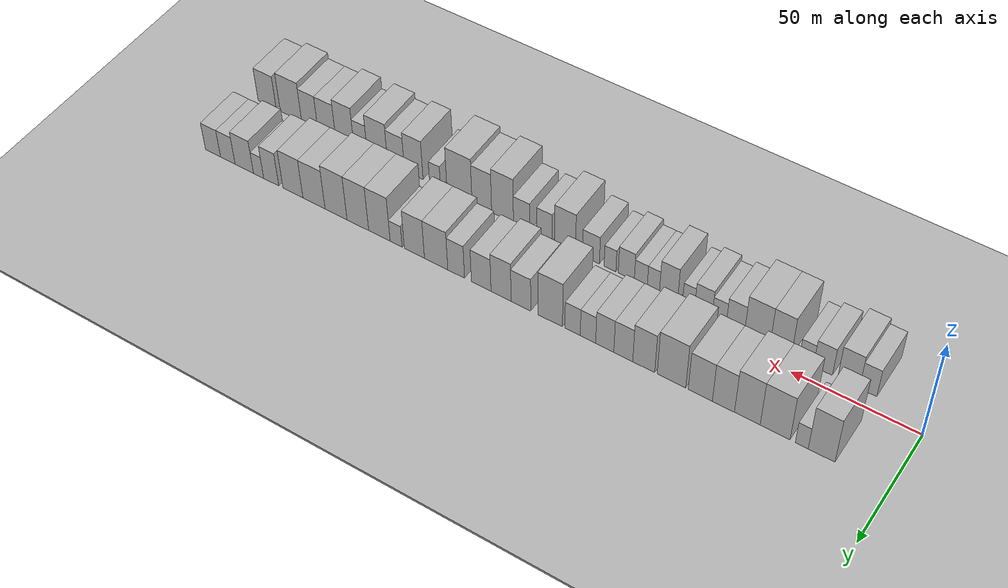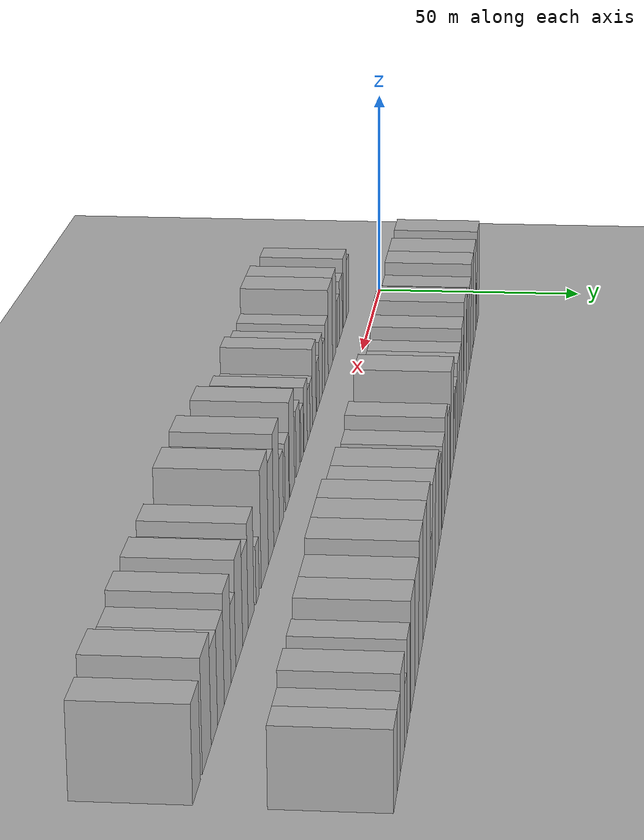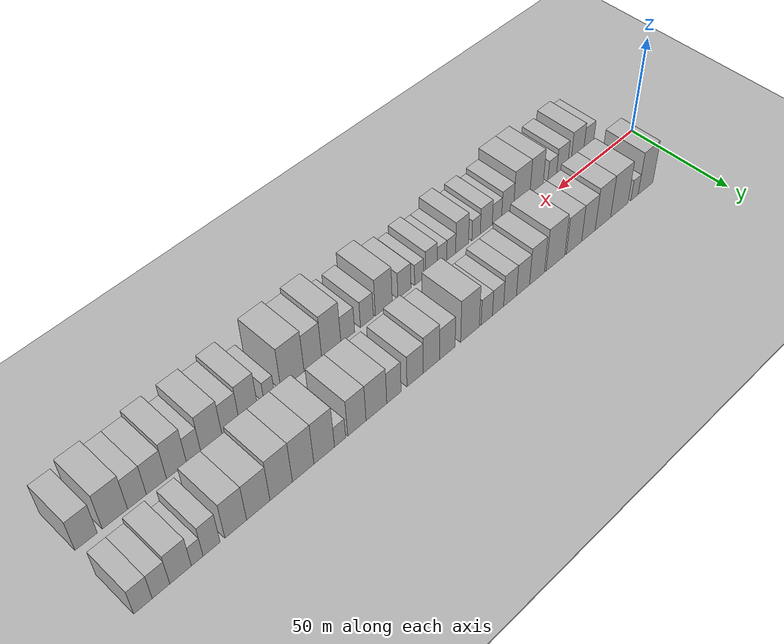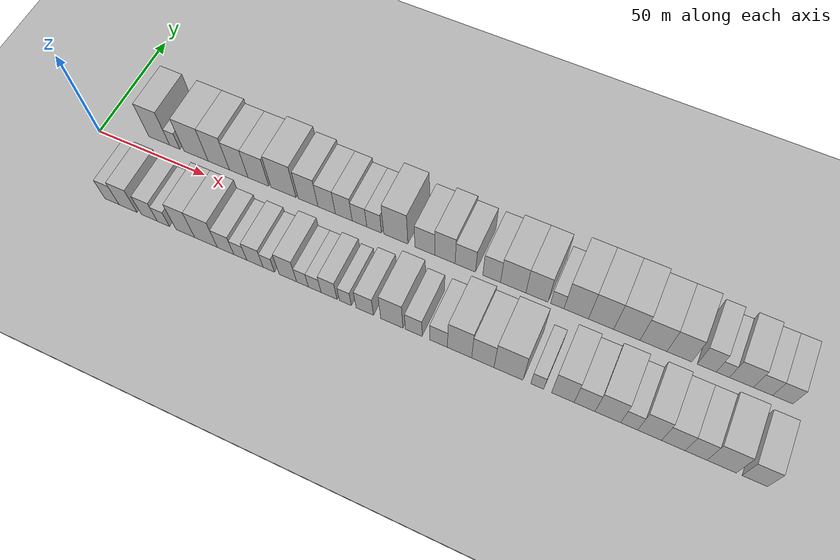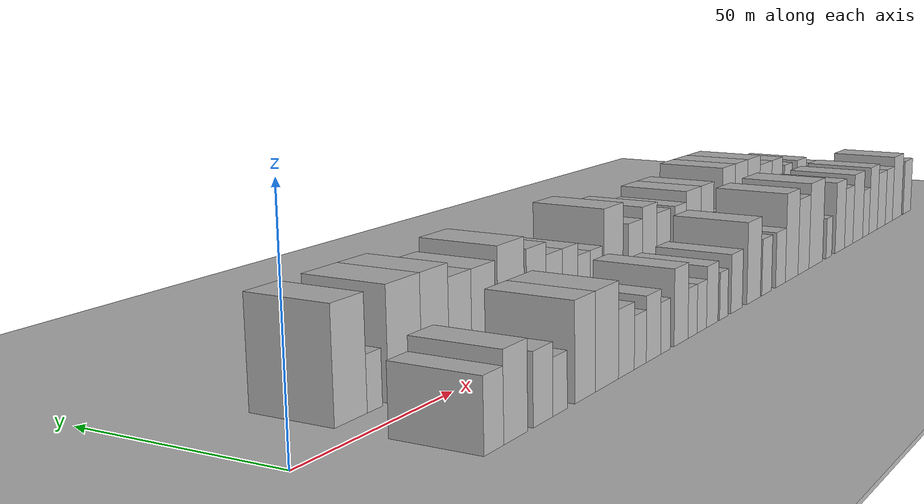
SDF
<?xml version="1.0" encoding="utf-8"?>

<sdf version="1.6">

   <world name="default">

      <gui fullscreen="0">

         <camera name="user_camera">

            <pose>-15 0 4.57585 0 0 0</pose>

            <view_controller>orbit</view_controller>

         </camera>

      </gui>

      <scene>

         <sky>

           <clouds>

             <speed>12</speed>

           </clouds>

         </sky>

         <ambient>0.4 0.4 0.4 1</ambient>

         <background>0.7 0.7 0.7 1</background>

         <shadows>1</shadows>

      </scene>

      <gravity>0 0 -9.8066</gravity>

      <magnetic_field>6e-06 2.3e-05 -4.2e-05</magnetic_field>

      <physics default="0" name="default_physics" type="ode">

         <ode>

            <solver>

               <type>quick</type>

               <iters>10</iters>

               <sor>1.0</sor>

               <use_dynamic_moi_rescaling>0</use_dynamic_moi_rescaling>

            </solver>

            <constraints>

               <cfm>0</cfm>

               <erp>0.2</erp>

               <contact_max_correcting_vel>100</contact_max_correcting_vel>

               <contact_surface_layer>0.001</contact_surface_layer>

            </constraints>

         </ode>

         <max_step_size>0.004</max_step_size>

         <real_time_factor>1</real_time_factor>

         <real_time_update_rate>250</real_time_update_rate>

      </physics>

      <light name="sun" type="directional">

         <cast_shadows>1</cast_shadows>

         <pose>0 0 10 0 0 0</pose>

         <diffuse>0.8 0.8 0.8 1</diffuse>

         <specular>0.2 0.2 0.2 1</specular>

         <attenuation>

            <range>1000</range>

            <constant>0.9</constant>

            <linear>0.01</linear>

            <quadratic>0.001</quadratic>

         </attenuation>

         <direction>-0.5 0.1 -0.9</direction>

      </light>

      <include>

         <name>ground_plane_1</name>

         <uri>model://HANNAS_ground_plane</uri>

         <pose>0 0 0  0 0 0</pose>

      </include>

      <include>

         <name>ground_plane_2</name>

         <uri>model://HANNAS_ground_plane</uri>

         <pose>100 0 0  0 0 0</pose>

      </include>

      <model name="building_1">

         <static>1</static>

         <pose frame="">25.0048 16.0000 0 0.000000 0.000000 1.570796</pose>

         <link name="link">

            <pose frame="">0 0 12.00 0 0 0</pose>

            <collision name="collision">

               <geometry>

                  <box>

                     <size>20.0000 10.0095 24.0000</size>

                  </box>

               </geometry>

               <max_contacts>10</max_contacts>

               <surface>

                  <contact>

                     <ode/>

                  </contact>

                  <bounce/>

                  <friction>

                     <torsional>

                        <ode/>

                     </torsional>

                     <ode/>

                  </friction>

               </surface>

            </collision>

            <visual name="visual">

               <cast_shadows>0</cast_shadows>

               <geometry>

                  <box>

                     <size>20.0000 10.0095 24.0000</size>

                  </box>

               </geometry>

               <material>

                  <script>

                     <uri>model://HANNAS_wall/materials/scripts</uri>

                     <uri>model://HANNAS_wall/materials/textures</uri>

                     <name>vrc/HANNAS_wall</name>

                  </script>

               </material>

            </visual>

            <self_collide>0</self_collide>

            <enable_wind>0</enable_wind>

            <kinematic>0</kinematic>

         </link>

      </model>

      <model name="building_2">

         <static>1</static>

         <pose frame="">32.4360 16.0000 0 0.000000 0.000000 1.570796</pose>

         <link name="link">

            <pose frame="">0 0 6.00 0 0 0</pose>

            <collision name="collision">

               <geometry>

                  <box>

                     <size>20.0000 4.8529 12.0000</size>

                  </box>

               </geometry>

               <max_contacts>10</max_contacts>

               <surface>

                  <contact>

                     <ode/>

                  </contact>

                  <bounce/>

                  <friction>

                     <torsional>

                        <ode/>

                     </torsional>

                     <ode/>

                  </friction>

               </surface>

            </collision>

            <visual name="visual">

               <cast_shadows>0</cast_shadows>

               <geometry>

                  <box>

                     <size>20.0000 4.8529 12.0000</size>

                  </box>

               </geometry>

               <material>

                  <script>

                     <uri>model://HANNAS_wall/materials/scripts</uri>

                     <uri>model://HANNAS_wall/materials/textures</uri>

                     <name>vrc/HANNAS_wall</name>

                  </script>

               </material>

            </visual>

            <self_collide>0</self_collide>

            <enable_wind>0</enable_wind>

            <kinematic>0</kinematic>

         </link>

      </model>

      <model name="building_3">

         <static>1</static>

         <pose frame="">42.5561 16.0000 0 0.000000 0.000000 1.570796</pose>

         <link name="link">

            <pose frame="">0 0 12.00 0 0 0</pose>

            <collision name="collision">

               <geometry>

                  <box>

                     <size>20.0000 11.3873 24.0000</size>

                  </box>

               </geometry>

               <max_contacts>10</max_contacts>

               <surface>

                  <contact>

                     <ode/>

                  </contact>

                  <bounce/>

                  <friction>

                     <torsional>

                        <ode/>

                     </torsional>

                     <ode/>

                  </friction>

               </surface>

            </collision>

            <visual name="visual">

               <cast_shadows>0</cast_shadows>

               <geometry>

                  <box>

                     <size>20.0000 11.3873 24.0000</size>

                  </box>

               </geometry>

               <material>

                  <script>

                     <uri>model://HANNAS_wall/materials/scripts</uri>

                     <uri>model://HANNAS_wall/materials/textures</uri>

                     <name>vrc/HANNAS_wall</name>

                  </script>

               </material>

            </visual>

            <self_collide>0</self_collide>

            <enable_wind>0</enable_wind>

            <kinematic>0</kinematic>

         </link>

      </model>

      <model name="building_4">

         <static>1</static>

         <pose frame="">53.2149 16.0000 0 0.000000 0.000000 1.570796</pose>

         <link name="link">

            <pose frame="">0 0 12.00 0 0 0</pose>

            <collision name="collision">

               <geometry>

                  <box>

                     <size>20.0000 9.9303 24.0000</size>

                  </box>

               </geometry>

               <max_contacts>10</max_contacts>

               <surface>

                  <contact>

                     <ode/>

                  </contact>

                  <bounce/>

                  <friction>

                     <torsional>

                        <ode/>

                     </torsional>

                     <ode/>

                  </friction>

               </surface>

            </collision>

            <visual name="visual">

               <cast_shadows>0</cast_shadows>

               <geometry>

                  <box>

                     <size>20.0000 9.9303 24.0000</size>

                  </box>

               </geometry>

               <material>

                  <script>

                     <uri>model://HANNAS_wall/materials/scripts</uri>

                     <uri>model://HANNAS_wall/materials/textures</uri>

                     <name>vrc/HANNAS_wall</name>

                  </script>

               </material>

            </visual>

            <self_collide>0</self_collide>

            <enable_wind>0</enable_wind>

            <kinematic>0</kinematic>

         </link>

      </model>

      <model name="building_5">

         <static>1</static>

         <pose frame="">62.4863 16.0000 0 0.000000 0.000000 1.570796</pose>

         <link name="link">

            <pose frame="">0 0 10.50 0 0 0</pose>

            <collision name="collision">

               <geometry>

                  <box>

                     <size>20.0000 8.6126 21.0000</size>

                  </box>

               </geometry>

               <max_contacts>10</max_contacts>

               <surface>

                  <contact>

                     <ode/>

                  </contact>

                  <bounce/>

                  <friction>

                     <torsional>

                        <ode/>

                     </torsional>

                     <ode/>

                  </friction>

               </surface>

            </collision>

            <visual name="visual">

               <cast_shadows>0</cast_shadows>

               <geometry>

                  <box>

                     <size>20.0000 8.6126 21.0000</size>

                  </box>

               </geometry>

               <material>

                  <script>

                     <uri>model://HANNAS_wall/materials/scripts</uri>

                     <uri>model://HANNAS_wall/materials/textures</uri>

                     <name>vrc/HANNAS_wall</name>

                  </script>

               </material>

            </visual>

            <self_collide>0</self_collide>

            <enable_wind>0</enable_wind>

            <kinematic>0</kinematic>

         </link>

      </model>

      <model name="building_6">

         <static>1</static>

         <pose frame="">71.5398 16.0000 0 0.000000 0.000000 1.570796</pose>

         <link name="link">

            <pose frame="">0 0 10.50 0 0 0</pose>

            <collision name="collision">

               <geometry>

                  <box>

                     <size>20.0000 9.4945 21.0000</size>

                  </box>

               </geometry>

               <max_contacts>10</max_contacts>

               <surface>

                  <contact>

                     <ode/>

                  </contact>

                  <bounce/>

                  <friction>

                     <torsional>

                        <ode/>

                     </torsional>

                     <ode/>

                  </friction>

               </surface>

            </collision>

            <visual name="visual">

               <cast_shadows>0</cast_shadows>

               <geometry>

                  <box>

                     <size>20.0000 9.4945 21.0000</size>

                  </box>

               </geometry>

               <material>

                  <script>

                     <uri>model://HANNAS_wall/materials/scripts</uri>

                     <uri>model://HANNAS_wall/materials/textures</uri>

                     <name>vrc/HANNAS_wall</name>

                  </script>

               </material>

            </visual>

            <self_collide>0</self_collide>

            <enable_wind>0</enable_wind>

            <kinematic>0</kinematic>

         </link>

      </model>

      <model name="building_7">

         <static>1</static>

         <pose frame="">82.9578 16.0000 0 0.000000 0.000000 1.570796</pose>

         <link name="link">

            <pose frame="">0 0 12.00 0 0 0</pose>

            <collision name="collision">

               <geometry>

                  <box>

                     <size>20.0000 11.3415 24.0000</size>

                  </box>

               </geometry>

               <max_contacts>10</max_contacts>

               <surface>

                  <contact>

                     <ode/>

                  </contact>

                  <bounce/>

                  <friction>

                     <torsional>

                        <ode/>

                     </torsional>

                     <ode/>

                  </friction>

               </surface>

            </collision>

            <visual name="visual">

               <cast_shadows>0</cast_shadows>

               <geometry>

                  <box>

                     <size>20.0000 11.3415 24.0000</size>

                  </box>

               </geometry>

               <material>

                  <script>

                     <uri>model://HANNAS_wall/materials/scripts</uri>

                     <uri>model://HANNAS_wall/materials/textures</uri>

                     <name>vrc/HANNAS_wall</name>

                  </script>

               </material>

            </visual>

            <self_collide>0</self_collide>

            <enable_wind>0</enable_wind>

            <kinematic>0</kinematic>

         </link>

      </model>

      <model name="building_8">

         <static>1</static>

         <pose frame="">94.0632 16.0000 0 0.000000 0.000000 1.570796</pose>

         <link name="link">

            <pose frame="">0 0 10.50 0 0 0</pose>

            <collision name="collision">

               <geometry>

                  <box>

                     <size>20.0000 8.8693 21.0000</size>

                  </box>

               </geometry>

               <max_contacts>10</max_contacts>

               <surface>

                  <contact>

                     <ode/>

                  </contact>

                  <bounce/>

                  <friction>

                     <torsional>

                        <ode/>

                     </torsional>

                     <ode/>

                  </friction>

               </surface>

            </collision>

            <visual name="visual">

               <cast_shadows>0</cast_shadows>

               <geometry>

                  <box>

                     <size>20.0000 8.8693 21.0000</size>

                  </box>

               </geometry>

               <material>

                  <script>

                     <uri>model://HANNAS_wall/materials/scripts</uri>

                     <uri>model://HANNAS_wall/materials/textures</uri>

                     <name>vrc/HANNAS_wall</name>

                  </script>

               </material>

            </visual>

            <self_collide>0</self_collide>

            <enable_wind>0</enable_wind>

            <kinematic>0</kinematic>

         </link>

      </model>

      <model name="building_9">

         <static>1</static>

         <pose frame="">102.3477 16.0000 0 0.000000 0.000000 1.570796</pose>

         <link name="link">

            <pose frame="">0 0 9.00 0 0 0</pose>

            <collision name="collision">

               <geometry>

                  <box>

                     <size>20.0000 7.6997 18.0000</size>

                  </box>

               </geometry>

               <max_contacts>10</max_contacts>

               <surface>

                  <contact>

                     <ode/>

                  </contact>

                  <bounce/>

                  <friction>

                     <torsional>

                        <ode/>

                     </torsional>

                     <ode/>

                  </friction>

               </surface>

            </collision>

            <visual name="visual">

               <cast_shadows>0</cast_shadows>

               <geometry>

                  <box>

                     <size>20.0000 7.6997 18.0000</size>

                  </box>

               </geometry>

               <material>

                  <script>

                     <uri>model://HANNAS_wall/materials/scripts</uri>

                     <uri>model://HANNAS_wall/materials/textures</uri>

                     <name>vrc/HANNAS_wall</name>

                  </script>

               </material>

            </visual>

            <self_collide>0</self_collide>

            <enable_wind>0</enable_wind>

            <kinematic>0</kinematic>

         </link>

      </model>

      <model name="building_10">

         <static>1</static>

         <pose frame="">109.9224 16.0000 0 0.000000 0.000000 1.570796</pose>

         <link name="link">

            <pose frame="">0 0 9.00 0 0 0</pose>

            <collision name="collision">

               <geometry>

                  <box>

                     <size>20.0000 7.4497 18.0000</size>

                  </box>

               </geometry>

               <max_contacts>10</max_contacts>

               <surface>

                  <contact>

                     <ode/>

                  </contact>

                  <bounce/>

                  <friction>

                     <torsional>

                        <ode/>

                     </torsional>

                     <ode/>

                  </friction>

               </surface>

            </collision>

            <visual name="visual">

               <cast_shadows>0</cast_shadows>

               <geometry>

                  <box>

                     <size>20.0000 7.4497 18.0000</size>

                  </box>

               </geometry>

               <material>

                  <script>

                     <uri>model://HANNAS_wall/materials/scripts</uri>

                     <uri>model://HANNAS_wall/materials/textures</uri>

                     <name>vrc/HANNAS_wall</name>

                  </script>

               </material>

            </visual>

            <self_collide>0</self_collide>

            <enable_wind>0</enable_wind>

            <kinematic>0</kinematic>

         </link>

      </model>

      <model name="building_11">

         <static>1</static>

         <pose frame="">116.8253 16.0000 0 0.000000 0.000000 1.570796</pose>

         <link name="link">

            <pose frame="">0 0 7.50 0 0 0</pose>

            <collision name="collision">

               <geometry>

                  <box>

                     <size>20.0000 6.3560 15.0000</size>

                  </box>

               </geometry>

               <max_contacts>10</max_contacts>

               <surface>

                  <contact>

                     <ode/>

                  </contact>

                  <bounce/>

                  <friction>

                     <torsional>

                        <ode/>

                     </torsional>

                     <ode/>

                  </friction>

               </surface>

            </collision>

            <visual name="visual">

               <cast_shadows>0</cast_shadows>

               <geometry>

                  <box>

                     <size>20.0000 6.3560 15.0000</size>

                  </box>

               </geometry>

               <material>

                  <script>

                     <uri>model://HANNAS_wall/materials/scripts</uri>

                     <uri>model://HANNAS_wall/materials/textures</uri>

                     <name>vrc/HANNAS_wall</name>

                  </script>

               </material>

            </visual>

            <self_collide>0</self_collide>

            <enable_wind>0</enable_wind>

            <kinematic>0</kinematic>

         </link>

      </model>

      <model name="building_12">

         <static>1</static>

         <pose frame="">123.1979 16.0000 0 0.000000 0.000000 1.570796</pose>

         <link name="link">

            <pose frame="">0 0 7.50 0 0 0</pose>

            <collision name="collision">

               <geometry>

                  <box>

                     <size>20.0000 6.3890 15.0000</size>

                  </box>

               </geometry>

               <max_contacts>10</max_contacts>

               <surface>

                  <contact>

                     <ode/>

                  </contact>

                  <bounce/>

                  <friction>

                     <torsional>

                        <ode/>

                     </torsional>

                     <ode/>

                  </friction>

               </surface>

            </collision>

            <visual name="visual">

               <cast_shadows>0</cast_shadows>

               <geometry>

                  <box>

                     <size>20.0000 6.3890 15.0000</size>

                  </box>

               </geometry>

               <material>

                  <script>

                     <uri>model://HANNAS_wall/materials/scripts</uri>

                     <uri>model://HANNAS_wall/materials/textures</uri>

                     <name>vrc/HANNAS_wall</name>

                  </script>

               </material>

            </visual>

            <self_collide>0</self_collide>

            <enable_wind>0</enable_wind>

            <kinematic>0</kinematic>

         </link>

      </model>

      <model name="building_13">

         <static>1</static>

         <pose frame="">132.5685 16.0000 0 0.000000 0.000000 1.570796</pose>

         <link name="link">

            <pose frame="">0 0 12.00 0 0 0</pose>

            <collision name="collision">

               <geometry>

                  <box>

                     <size>20.0000 10.3522 24.0000</size>

                  </box>

               </geometry>

               <max_contacts>10</max_contacts>

               <surface>

                  <contact>

                     <ode/>

                  </contact>

                  <bounce/>

                  <friction>

                     <torsional>

                        <ode/>

                     </torsional>

                     <ode/>

                  </friction>

               </surface>

            </collision>

            <visual name="visual">

               <cast_shadows>0</cast_shadows>

               <geometry>

                  <box>

                     <size>20.0000 10.3522 24.0000</size>

                  </box>

               </geometry>

               <material>

                  <script>

                     <uri>model://HANNAS_wall/materials/scripts</uri>

                     <uri>model://HANNAS_wall/materials/textures</uri>

                     <name>vrc/HANNAS_wall</name>

                  </script>

               </material>

            </visual>

            <self_collide>0</self_collide>

            <enable_wind>0</enable_wind>

            <kinematic>0</kinematic>

         </link>

      </model>

      <model name="building_14">

         <static>1</static>

         <pose frame="">144.9226 16.0000 0 0.000000 0.000000 1.570796</pose>

         <link name="link">

            <pose frame="">0 0 9.00 0 0 0</pose>

            <collision name="collision">

               <geometry>

                  <box>

                     <size>20.0000 8.3561 18.0000</size>

                  </box>

               </geometry>

               <max_contacts>10</max_contacts>

               <surface>

                  <contact>

                     <ode/>

                  </contact>

                  <bounce/>

                  <friction>

                     <torsional>

                        <ode/>

                     </torsional>

                     <ode/>

                  </friction>

               </surface>

            </collision>

            <visual name="visual">

               <cast_shadows>0</cast_shadows>

               <geometry>

                  <box>

                     <size>20.0000 8.3561 18.0000</size>

                  </box>

               </geometry>

               <material>

                  <script>

                     <uri>model://HANNAS_wall/materials/scripts</uri>

                     <uri>model://HANNAS_wall/materials/textures</uri>

                     <name>vrc/HANNAS_wall</name>

                  </script>

               </material>

            </visual>

            <self_collide>0</self_collide>

            <enable_wind>0</enable_wind>

            <kinematic>0</kinematic>

         </link>

      </model>

      <model name="building_15">

         <static>1</static>

         <pose frame="">153.4222 16.0000 0 0.000000 0.000000 1.570796</pose>

         <link name="link">

            <pose frame="">0 0 10.50 0 0 0</pose>

            <collision name="collision">

               <geometry>

                  <box>

                     <size>20.0000 8.6431 21.0000</size>

                  </box>

               </geometry>

               <max_contacts>10</max_contacts>

               <surface>

                  <contact>

                     <ode/>

                  </contact>

                  <bounce/>

                  <friction>

                     <torsional>

                        <ode/>

                     </torsional>

                     <ode/>

                  </friction>

               </surface>

            </collision>

            <visual name="visual">

               <cast_shadows>0</cast_shadows>

               <geometry>

                  <box>

                     <size>20.0000 8.6431 21.0000</size>

                  </box>

               </geometry>

               <material>

                  <script>

                     <uri>model://HANNAS_wall/materials/scripts</uri>

                     <uri>model://HANNAS_wall/materials/textures</uri>

                     <name>vrc/HANNAS_wall</name>

                  </script>

               </material>

            </visual>

            <self_collide>0</self_collide>

            <enable_wind>0</enable_wind>

            <kinematic>0</kinematic>

         </link>

      </model>

      <model name="building_16">

         <static>1</static>

         <pose frame="">161.9941 16.0000 0 0.000000 0.000000 1.570796</pose>

         <link name="link">

            <pose frame="">0 0 9.00 0 0 0</pose>

            <collision name="collision">

               <geometry>

                  <box>

                     <size>20.0000 8.5007 18.0000</size>

                  </box>

               </geometry>

               <max_contacts>10</max_contacts>

               <surface>

                  <contact>

                     <ode/>

                  </contact>

                  <bounce/>

                  <friction>

                     <torsional>

                        <ode/>

                     </torsional>

                     <ode/>

                  </friction>

               </surface>

            </collision>

            <visual name="visual">

               <cast_shadows>0</cast_shadows>

               <geometry>

                  <box>

                     <size>20.0000 8.5007 18.0000</size>

                  </box>

               </geometry>

               <material>

                  <script>

                     <uri>model://HANNAS_wall/materials/scripts</uri>

                     <uri>model://HANNAS_wall/materials/textures</uri>

                     <name>vrc/HANNAS_wall</name>

                  </script>

               </material>

            </visual>

            <self_collide>0</self_collide>

            <enable_wind>0</enable_wind>

            <kinematic>0</kinematic>

         </link>

      </model>

      <model name="building_17">

         <static>1</static>

         <pose frame="">172.9062 16.0000 0 0.000000 0.000000 1.570796</pose>

         <link name="link">

            <pose frame="">0 0 9.00 0 0 0</pose>

            <collision name="collision">

               <geometry>

                  <box>

                     <size>20.0000 7.3235 18.0000</size>

                  </box>

               </geometry>

               <max_contacts>10</max_contacts>

               <surface>

                  <contact>

                     <ode/>

                  </contact>

                  <bounce/>

                  <friction>

                     <torsional>

                        <ode/>

                     </torsional>

                     <ode/>

                  </friction>

               </surface>

            </collision>

            <visual name="visual">

               <cast_shadows>0</cast_shadows>

               <geometry>

                  <box>

                     <size>20.0000 7.3235 18.0000</size>

                  </box>

               </geometry>

               <material>

                  <script>

                     <uri>model://HANNAS_wall/materials/scripts</uri>

                     <uri>model://HANNAS_wall/materials/textures</uri>

                     <name>vrc/HANNAS_wall</name>

                  </script>

               </material>

            </visual>

            <self_collide>0</self_collide>

            <enable_wind>0</enable_wind>

            <kinematic>0</kinematic>

         </link>

      </model>

      <model name="building_18">

         <static>1</static>

         <pose frame="">181.7380 16.0000 0 0.000000 0.000000 1.570796</pose>

         <link name="link">

            <pose frame="">0 0 10.50 0 0 0</pose>

            <collision name="collision">

               <geometry>

                  <box>

                     <size>20.0000 10.3401 21.0000</size>

                  </box>

               </geometry>

               <max_contacts>10</max_contacts>

               <surface>

                  <contact>

                     <ode/>

                  </contact>

                  <bounce/>

                  <friction>

                     <torsional>

                        <ode/>

                     </torsional>

                     <ode/>

                  </friction>

               </surface>

            </collision>

            <visual name="visual">

               <cast_shadows>0</cast_shadows>

               <geometry>

                  <box>

                     <size>20.0000 10.3401 21.0000</size>

                  </box>

               </geometry>

               <material>

                  <script>

                     <uri>model://HANNAS_wall/materials/scripts</uri>

                     <uri>model://HANNAS_wall/materials/textures</uri>

                     <name>vrc/HANNAS_wall</name>

                  </script>

               </material>

            </visual>

            <self_collide>0</self_collide>

            <enable_wind>0</enable_wind>

            <kinematic>0</kinematic>

         </link>

      </model>

      <model name="building_19">

         <static>1</static>

         <pose frame="">191.3927 16.0000 0 0.000000 0.000000 1.570796</pose>

         <link name="link">

            <pose frame="">0 0 10.50 0 0 0</pose>

            <collision name="collision">

               <geometry>

                  <box>

                     <size>20.0000 8.9692 21.0000</size>

                  </box>

               </geometry>

               <max_contacts>10</max_contacts>

               <surface>

                  <contact>

                     <ode/>

                  </contact>

                  <bounce/>

                  <friction>

                     <torsional>

                        <ode/>

                     </torsional>

                     <ode/>

                  </friction>

               </surface>

            </collision>

            <visual name="visual">

               <cast_shadows>0</cast_shadows>

               <geometry>

                  <box>

                     <size>20.0000 8.9692 21.0000</size>

                  </box>

               </geometry>

               <material>

                  <script>

                     <uri>model://HANNAS_wall/materials/scripts</uri>

                     <uri>model://HANNAS_wall/materials/textures</uri>

                     <name>vrc/HANNAS_wall</name>

                  </script>

               </material>

            </visual>

            <self_collide>0</self_collide>

            <enable_wind>0</enable_wind>

            <kinematic>0</kinematic>

         </link>

      </model>

      <model name="building_20">

         <static>1</static>

         <pose frame="">199.5718 16.0000 0 0.000000 0.000000 1.570796</pose>

         <link name="link">

            <pose frame="">0 0 6.00 0 0 0</pose>

            <collision name="collision">

               <geometry>

                  <box>

                     <size>20.0000 5.3890 12.0000</size>

                  </box>

               </geometry>

               <max_contacts>10</max_contacts>

               <surface>

                  <contact>

                     <ode/>

                  </contact>

                  <bounce/>

                  <friction>

                     <torsional>

                        <ode/>

                     </torsional>

                     <ode/>

                  </friction>

               </surface>

            </collision>

            <visual name="visual">

               <cast_shadows>0</cast_shadows>

               <geometry>

                  <box>

                     <size>20.0000 5.3890 12.0000</size>

                  </box>

               </geometry>

               <material>

                  <script>

                     <uri>model://HANNAS_wall/materials/scripts</uri>

                     <uri>model://HANNAS_wall/materials/textures</uri>

                     <name>vrc/HANNAS_wall</name>

                  </script>

               </material>

            </visual>

            <self_collide>0</self_collide>

            <enable_wind>0</enable_wind>

            <kinematic>0</kinematic>

         </link>

      </model>

      <model name="building_21">

         <static>1</static>

         <pose frame="">207.1382 16.0000 0 0.000000 0.000000 1.570796</pose>

         <link name="link">

            <pose frame="">0 0 12.00 0 0 0</pose>

            <collision name="collision">

               <geometry>

                  <box>

                     <size>20.0000 9.7437 24.0000</size>

                  </box>

               </geometry>

               <max_contacts>10</max_contacts>

               <surface>

                  <contact>

                     <ode/>

                  </contact>

                  <bounce/>

                  <friction>

                     <torsional>

                        <ode/>

                     </torsional>

                     <ode/>

                  </friction>

               </surface>

            </collision>

            <visual name="visual">

               <cast_shadows>0</cast_shadows>

               <geometry>

                  <box>

                     <size>20.0000 9.7437 24.0000</size>

                  </box>

               </geometry>

               <material>

                  <script>

                     <uri>model://HANNAS_wall/materials/scripts</uri>

                     <uri>model://HANNAS_wall/materials/textures</uri>

                     <name>vrc/HANNAS_wall</name>

                  </script>

               </material>

            </visual>

            <self_collide>0</self_collide>

            <enable_wind>0</enable_wind>

            <kinematic>0</kinematic>

         </link>

      </model>

      <model name="building_22">

         <static>1</static>

         <pose frame="">216.9790 16.0000 0 0.000000 0.000000 1.570796</pose>

         <link name="link">

            <pose frame="">0 0 12.00 0 0 0</pose>

            <collision name="collision">

               <geometry>

                  <box>

                     <size>20.0000 9.9380 24.0000</size>

                  </box>

               </geometry>

               <max_contacts>10</max_contacts>

               <surface>

                  <contact>

                     <ode/>

                  </contact>

                  <bounce/>

                  <friction>

                     <torsional>

                        <ode/>

                     </torsional>

                     <ode/>

                  </friction>

               </surface>

            </collision>

            <visual name="visual">

               <cast_shadows>0</cast_shadows>

               <geometry>

                  <box>

                     <size>20.0000 9.9380 24.0000</size>

                  </box>

               </geometry>

               <material>

                  <script>

                     <uri>model://HANNAS_wall/materials/scripts</uri>

                     <uri>model://HANNAS_wall/materials/textures</uri>

                     <name>vrc/HANNAS_wall</name>

                  </script>

               </material>

            </visual>

            <self_collide>0</self_collide>

            <enable_wind>0</enable_wind>

            <kinematic>0</kinematic>

         </link>

      </model>

      <model name="building_23">

         <static>1</static>

         <pose frame="">227.0366 16.0000 0 0.000000 0.000000 1.570796</pose>

         <link name="link">

            <pose frame="">0 0 12.00 0 0 0</pose>

            <collision name="collision">

               <geometry>

                  <box>

                     <size>20.0000 10.1770 24.0000</size>

                  </box>

               </geometry>

               <max_contacts>10</max_contacts>

               <surface>

                  <contact>

                     <ode/>

                  </contact>

                  <bounce/>

                  <friction>

                     <torsional>

                        <ode/>

                     </torsional>

                     <ode/>

                  </friction>

               </surface>

            </collision>

            <visual name="visual">

               <cast_shadows>0</cast_shadows>

               <geometry>

                  <box>

                     <size>20.0000 10.1770 24.0000</size>

                  </box>

               </geometry>

               <material>

                  <script>

                     <uri>model://HANNAS_wall/materials/scripts</uri>

                     <uri>model://HANNAS_wall/materials/textures</uri>

                     <name>vrc/HANNAS_wall</name>

                  </script>

               </material>

            </visual>

            <self_collide>0</self_collide>

            <enable_wind>0</enable_wind>

            <kinematic>0</kinematic>

         </link>

      </model>

      <model name="building_24">

         <static>1</static>

         <pose frame="">237.3103 16.0000 0 0.000000 0.000000 1.570796</pose>

         <link name="link">

            <pose frame="">0 0 10.50 0 0 0</pose>

            <collision name="collision">

               <geometry>

                  <box>

                     <size>20.0000 10.3703 21.0000</size>

                  </box>

               </geometry>

               <max_contacts>10</max_contacts>

               <surface>

                  <contact>

                     <ode/>

                  </contact>

                  <bounce/>

                  <friction>

                     <torsional>

                        <ode/>

                     </torsional>

                     <ode/>

                  </friction>

               </surface>

            </collision>

            <visual name="visual">

               <cast_shadows>0</cast_shadows>

               <geometry>

                  <box>

                     <size>20.0000 10.3703 21.0000</size>

                  </box>

               </geometry>

               <material>

                  <script>

                     <uri>model://HANNAS_wall/materials/scripts</uri>

                     <uri>model://HANNAS_wall/materials/textures</uri>

                     <name>vrc/HANNAS_wall</name>

                  </script>

               </material>

            </visual>

            <self_collide>0</self_collide>

            <enable_wind>0</enable_wind>

            <kinematic>0</kinematic>

         </link>

      </model>

      <model name="building_25">

         <static>1</static>

         <pose frame="">247.2131 16.0000 0 0.000000 0.000000 1.570796</pose>

         <link name="link">

            <pose frame="">0 0 10.50 0 0 0</pose>

            <collision name="collision">

               <geometry>

                  <box>

                     <size>20.0000 9.4353 21.0000</size>

                  </box>

               </geometry>

               <max_contacts>10</max_contacts>

               <surface>

                  <contact>

                     <ode/>

                  </contact>

                  <bounce/>

                  <friction>

                     <torsional>

                        <ode/>

                     </torsional>

                     <ode/>

                  </friction>

               </surface>

            </collision>

            <visual name="visual">

               <cast_shadows>0</cast_shadows>

               <geometry>

                  <box>

                     <size>20.0000 9.4353 21.0000</size>

                  </box>

               </geometry>

               <material>

                  <script>

                     <uri>model://HANNAS_wall/materials/scripts</uri>

                     <uri>model://HANNAS_wall/materials/textures</uri>

                     <name>vrc/HANNAS_wall</name>

                  </script>

               </material>

            </visual>

            <self_collide>0</self_collide>

            <enable_wind>0</enable_wind>

            <kinematic>0</kinematic>

         </link>

      </model>

      <model name="building_26">

         <static>1</static>

         <pose frame="">257.5350 16.0000 0 0.000000 0.000000 1.570796</pose>

         <link name="link">

            <pose frame="">0 0 9.00 0 0 0</pose>

            <collision name="collision">

               <geometry>

                  <box>

                     <size>20.0000 7.2085 18.0000</size>

                  </box>

               </geometry>

               <max_contacts>10</max_contacts>

               <surface>

                  <contact>

                     <ode/>

                  </contact>

                  <bounce/>

                  <friction>

                     <torsional>

                        <ode/>

                     </torsional>

                     <ode/>

                  </friction>

               </surface>

            </collision>

            <visual name="visual">

               <cast_shadows>0</cast_shadows>

               <geometry>

                  <box>

                     <size>20.0000 7.2085 18.0000</size>

                  </box>

               </geometry>

               <material>

                  <script>

                     <uri>model://HANNAS_wall/materials/scripts</uri>

                     <uri>model://HANNAS_wall/materials/textures</uri>

                     <name>vrc/HANNAS_wall</name>

                  </script>

               </material>

            </visual>

            <self_collide>0</self_collide>

            <enable_wind>0</enable_wind>

            <kinematic>0</kinematic>

         </link>

      </model>

      <model name="building_27">

         <static>1</static>

         <pose frame="">263.5808 16.0000 0 0.000000 0.000000 1.570796</pose>

         <link name="link">

            <pose frame="">0 0 6.00 0 0 0</pose>

            <collision name="collision">

               <geometry>

                  <box>

                     <size>20.0000 4.8830 12.0000</size>

                  </box>

               </geometry>

               <max_contacts>10</max_contacts>

               <surface>

                  <contact>

                     <ode/>

                  </contact>

                  <bounce/>

                  <friction>

                     <torsional>

                        <ode/>

                     </torsional>

                     <ode/>

                  </friction>

               </surface>

            </collision>

            <visual name="visual">

               <cast_shadows>0</cast_shadows>

               <geometry>

                  <box>

                     <size>20.0000 4.8830 12.0000</size>

                  </box>

               </geometry>

               <material>

                  <script>

                     <uri>model://HANNAS_wall/materials/scripts</uri>

                     <uri>model://HANNAS_wall/materials/textures</uri>

                     <name>vrc/HANNAS_wall</name>

                  </script>

               </material>

            </visual>

            <self_collide>0</self_collide>

            <enable_wind>0</enable_wind>

            <kinematic>0</kinematic>

         </link>

      </model>

      <model name="building_28">

         <static>1</static>

         <pose frame="">270.4634 16.0000 0 0.000000 0.000000 1.570796</pose>

         <link name="link">

            <pose frame="">0 0 9.00 0 0 0</pose>

            <collision name="collision">

               <geometry>

                  <box>

                     <size>20.0000 8.8822 18.0000</size>

                  </box>

               </geometry>

               <max_contacts>10</max_contacts>

               <surface>

                  <contact>

                     <ode/>

                  </contact>

                  <bounce/>

                  <friction>

                     <torsional>

                        <ode/>

                     </torsional>

                     <ode/>

                  </friction>

               </surface>

            </collision>

            <visual name="visual">

               <cast_shadows>0</cast_shadows>

               <geometry>

                  <box>

                     <size>20.0000 8.8822 18.0000</size>

                  </box>

               </geometry>

               <material>

                  <script>

                     <uri>model://HANNAS_wall/materials/scripts</uri>

                     <uri>model://HANNAS_wall/materials/textures</uri>

                     <name>vrc/HANNAS_wall</name>

                  </script>

               </material>

            </visual>

            <self_collide>0</self_collide>

            <enable_wind>0</enable_wind>

            <kinematic>0</kinematic>

         </link>

      </model>

      <model name="building_29">

         <static>1</static>

         <pose frame="">278.4469 16.0000 0 0.000000 0.000000 1.570796</pose>

         <link name="link">

            <pose frame="">0 0 7.50 0 0 0</pose>

            <collision name="collision">

               <geometry>

                  <box>

                     <size>20.0000 7.0848 15.0000</size>

                  </box>

               </geometry>

               <max_contacts>10</max_contacts>

               <surface>

                  <contact>

                     <ode/>

                  </contact>

                  <bounce/>

                  <friction>

                     <torsional>

                        <ode/>

                     </torsional>

                     <ode/>

                  </friction>

               </surface>

            </collision>

            <visual name="visual">

               <cast_shadows>0</cast_shadows>

               <geometry>

                  <box>

                     <size>20.0000 7.0848 15.0000</size>

                  </box>

               </geometry>

               <material>

                  <script>

                     <uri>model://HANNAS_wall/materials/scripts</uri>

                     <uri>model://HANNAS_wall/materials/textures</uri>

                     <name>vrc/HANNAS_wall</name>

                  </script>

               </material>

            </visual>

            <self_collide>0</self_collide>

            <enable_wind>0</enable_wind>

            <kinematic>0</kinematic>

         </link>

      </model>

      <model name="building_30">

         <static>1</static>

         <pose frame="">285.6913 16.0000 0 0.000000 0.000000 1.570796</pose>

         <link name="link">

            <pose frame="">0 0 7.50 0 0 0</pose>

            <collision name="collision">

               <geometry>

                  <box>

                     <size>20.0000 7.4039 15.0000</size>

                  </box>

               </geometry>

               <max_contacts>10</max_contacts>

               <surface>

                  <contact>

                     <ode/>

                  </contact>

                  <bounce/>

                  <friction>

                     <torsional>

                        <ode/>

                     </torsional>

                     <ode/>

                  </friction>

               </surface>

            </collision>

            <visual name="visual">

               <cast_shadows>0</cast_shadows>

               <geometry>

                  <box>

                     <size>20.0000 7.4039 15.0000</size>

                  </box>

               </geometry>

               <material>

                  <script>

                     <uri>model://HANNAS_wall/materials/scripts</uri>

                     <uri>model://HANNAS_wall/materials/textures</uri>

                     <name>vrc/HANNAS_wall</name>

                  </script>

               </material>

            </visual>

            <self_collide>0</self_collide>

            <enable_wind>0</enable_wind>

            <kinematic>0</kinematic>

         </link>

      </model>

      <model name="building_31">

         <static>1</static>

         <pose frame="">23.3150 -16.0000 0 0.000000 0.000000 1.570796</pose>

         <link name="link">

            <pose frame="">0 0 7.50 0 0 0</pose>

            <collision name="collision">

               <geometry>

                  <box>

                     <size>20.0000 6.6299 15.0000</size>

                  </box>

               </geometry>

               <max_contacts>10</max_contacts>

               <surface>

                  <contact>

                     <ode/>

                  </contact>

                  <bounce/>

                  <friction>

                     <torsional>

                        <ode/>

                     </torsional>

                     <ode/>

                  </friction>

               </surface>

            </collision>

            <visual name="visual">

               <cast_shadows>0</cast_shadows>

               <geometry>

                  <box>

                     <size>20.0000 6.6299 15.0000</size>

                  </box>

               </geometry>

               <material>

                  <script>

                     <uri>model://HANNAS_wall/materials/scripts</uri>

                     <uri>model://HANNAS_wall/materials/textures</uri>

                     <name>vrc/HANNAS_wall</name>

                  </script>

               </material>

            </visual>

            <self_collide>0</self_collide>

            <enable_wind>0</enable_wind>

            <kinematic>0</kinematic>

         </link>

      </model>

      <model name="building_32">

         <static>1</static>

         <pose frame="">30.8059 -16.0000 0 0.000000 0.000000 1.570796</pose>

         <link name="link">

            <pose frame="">0 0 9.00 0 0 0</pose>

            <collision name="collision">

               <geometry>

                  <box>

                     <size>20.0000 8.3519 18.0000</size>

                  </box>

               </geometry>

               <max_contacts>10</max_contacts>

               <surface>

                  <contact>

                     <ode/>

                  </contact>

                  <bounce/>

                  <friction>

                     <torsional>

                        <ode/>

                     </torsional>

                     <ode/>

                  </friction>

               </surface>

            </collision>

            <visual name="visual">

               <cast_shadows>0</cast_shadows>

               <geometry>

                  <box>

                     <size>20.0000 8.3519 18.0000</size>

                  </box>

               </geometry>

               <material>

                  <script>

                     <uri>model://HANNAS_wall/materials/scripts</uri>

                     <uri>model://HANNAS_wall/materials/textures</uri>

                     <name>vrc/HANNAS_wall</name>

                  </script>

               </material>

            </visual>

            <self_collide>0</self_collide>

            <enable_wind>0</enable_wind>

            <kinematic>0</kinematic>

         </link>

      </model>

      <model name="building_33">

         <static>1</static>

         <pose frame="">40.6561 -16.0000 0 0.000000 0.000000 1.570796</pose>

         <link name="link">

            <pose frame="">0 0 7.50 0 0 0</pose>

            <collision name="collision">

               <geometry>

                  <box>

                     <size>20.0000 7.3485 15.0000</size>

                  </box>

               </geometry>

               <max_contacts>10</max_contacts>

               <surface>

                  <contact>

                     <ode/>

                  </contact>

                  <bounce/>

                  <friction>

                     <torsional>

                        <ode/>

                     </torsional>

                     <ode/>

                  </friction>

               </surface>

            </collision>

            <visual name="visual">

               <cast_shadows>0</cast_shadows>

               <geometry>

                  <box>

                     <size>20.0000 7.3485 15.0000</size>

                  </box>

               </geometry>

               <material>

                  <script>

                     <uri>model://HANNAS_wall/materials/scripts</uri>

                     <uri>model://HANNAS_wall/materials/textures</uri>

                     <name>vrc/HANNAS_wall</name>

                  </script>

               </material>

            </visual>

            <self_collide>0</self_collide>

            <enable_wind>0</enable_wind>

            <kinematic>0</kinematic>

         </link>

      </model>

      <model name="building_34">

         <static>1</static>

         <pose frame="">47.1255 -16.0000 0 0.000000 0.000000 1.570796</pose>

         <link name="link">

            <pose frame="">0 0 6.00 0 0 0</pose>

            <collision name="collision">

               <geometry>

                  <box>

                     <size>20.0000 5.5903 12.0000</size>

                  </box>

               </geometry>

               <max_contacts>10</max_contacts>

               <surface>

                  <contact>

                     <ode/>

                  </contact>

                  <bounce/>

                  <friction>

                     <torsional>

                        <ode/>

                     </torsional>

                     <ode/>

                  </friction>

               </surface>

            </collision>

            <visual name="visual">

               <cast_shadows>0</cast_shadows>

               <geometry>

                  <box>

                     <size>20.0000 5.5903 12.0000</size>

                  </box>

               </geometry>

               <material>

                  <script>

                     <uri>model://HANNAS_wall/materials/scripts</uri>

                     <uri>model://HANNAS_wall/materials/textures</uri>

                     <name>vrc/HANNAS_wall</name>

                  </script>

               </material>

            </visual>

            <self_collide>0</self_collide>

            <enable_wind>0</enable_wind>

            <kinematic>0</kinematic>

         </link>

      </model>

      <model name="building_35">

         <static>1</static>

         <pose frame="">57.1463 -16.0000 0 0.000000 0.000000 1.570796</pose>

         <link name="link">

            <pose frame="">0 0 10.50 0 0 0</pose>

            <collision name="collision">

               <geometry>

                  <box>

                     <size>20.0000 8.4513 21.0000</size>

                  </box>

               </geometry>

               <max_contacts>10</max_contacts>

               <surface>

                  <contact>

                     <ode/>

                  </contact>

                  <bounce/>

                  <friction>

                     <torsional>

                        <ode/>

                     </torsional>

                     <ode/>

                  </friction>

               </surface>

            </collision>

            <visual name="visual">

               <cast_shadows>0</cast_shadows>

               <geometry>

                  <box>

                     <size>20.0000 8.4513 21.0000</size>

                  </box>

               </geometry>

               <material>

                  <script>

                     <uri>model://HANNAS_wall/materials/scripts</uri>

                     <uri>model://HANNAS_wall/materials/textures</uri>

                     <name>vrc/HANNAS_wall</name>

                  </script>

               </material>

            </visual>

            <self_collide>0</self_collide>

            <enable_wind>0</enable_wind>

            <kinematic>0</kinematic>

         </link>

      </model>

      <model name="building_36">

         <static>1</static>

         <pose frame="">66.4636 -16.0000 0 0.000000 0.000000 1.570796</pose>

         <link name="link">

            <pose frame="">0 0 10.50 0 0 0</pose>

            <collision name="collision">

               <geometry>

                  <box>

                     <size>20.0000 10.1834 21.0000</size>

                  </box>

               </geometry>

               <max_contacts>10</max_contacts>

               <surface>

                  <contact>

                     <ode/>

                  </contact>

                  <bounce/>

                  <friction>

                     <torsional>

                        <ode/>

                     </torsional>

                     <ode/>

                  </friction>

               </surface>

            </collision>

            <visual name="visual">

               <cast_shadows>0</cast_shadows>

               <geometry>

                  <box>

                     <size>20.0000 10.1834 21.0000</size>

                  </box>

               </geometry>

               <material>

                  <script>

                     <uri>model://HANNAS_wall/materials/scripts</uri>

                     <uri>model://HANNAS_wall/materials/textures</uri>

                     <name>vrc/HANNAS_wall</name>

                  </script>

               </material>

            </visual>

            <self_collide>0</self_collide>

            <enable_wind>0</enable_wind>

            <kinematic>0</kinematic>

         </link>

      </model>

      <model name="building_37">

         <static>1</static>

         <pose frame="">75.2245 -16.0000 0 0.000000 0.000000 1.570796</pose>

         <link name="link">

            <pose frame="">0 0 7.50 0 0 0</pose>

            <collision name="collision">

               <geometry>

                  <box>

                     <size>20.0000 7.3383 15.0000</size>

                  </box>

               </geometry>

               <max_contacts>10</max_contacts>

               <surface>

                  <contact>

                     <ode/>

                  </contact>

                  <bounce/>

                  <friction>

                     <torsional>

                        <ode/>

                     </torsional>

                     <ode/>

                  </friction>

               </surface>

            </collision>

            <visual name="visual">

               <cast_shadows>0</cast_shadows>

               <geometry>

                  <box>

                     <size>20.0000 7.3383 15.0000</size>

                  </box>

               </geometry>

               <material>

                  <script>

                     <uri>model://HANNAS_wall/materials/scripts</uri>

                     <uri>model://HANNAS_wall/materials/textures</uri>

                     <name>vrc/HANNAS_wall</name>

                  </script>

               </material>

            </visual>

            <self_collide>0</self_collide>

            <enable_wind>0</enable_wind>

            <kinematic>0</kinematic>

         </link>

      </model>

      <model name="building_38">

         <static>1</static>

         <pose frame="">81.7607 -16.0000 0 0.000000 0.000000 1.570796</pose>

         <link name="link">

            <pose frame="">0 0 6.00 0 0 0</pose>

            <collision name="collision">

               <geometry>

                  <box>

                     <size>20.0000 5.7341 12.0000</size>

                  </box>

               </geometry>

               <max_contacts>10</max_contacts>

               <surface>

                  <contact>

                     <ode/>

                  </contact>

                  <bounce/>

                  <friction>

                     <torsional>

                        <ode/>

                     </torsional>

                     <ode/>

                  </friction>

               </surface>

            </collision>

            <visual name="visual">

               <cast_shadows>0</cast_shadows>

               <geometry>

                  <box>

                     <size>20.0000 5.7341 12.0000</size>

                  </box>

               </geometry>

               <material>

                  <script>

                     <uri>model://HANNAS_wall/materials/scripts</uri>

                     <uri>model://HANNAS_wall/materials/textures</uri>

                     <name>vrc/HANNAS_wall</name>

                  </script>

               </material>

            </visual>

            <self_collide>0</self_collide>

            <enable_wind>0</enable_wind>

            <kinematic>0</kinematic>

         </link>

      </model>

      <model name="building_39">

         <static>1</static>

         <pose frame="">88.1978 -16.0000 0 0.000000 0.000000 1.570796</pose>

         <link name="link">

            <pose frame="">0 0 7.50 0 0 0</pose>

            <collision name="collision">

               <geometry>

                  <box>

                     <size>20.0000 7.1402 15.0000</size>

                  </box>

               </geometry>

               <max_contacts>10</max_contacts>

               <surface>

                  <contact>

                     <ode/>

                  </contact>

                  <bounce/>

                  <friction>

                     <torsional>

                        <ode/>

                     </torsional>

                     <ode/>

                  </friction>

               </surface>

            </collision>

            <visual name="visual">

               <cast_shadows>0</cast_shadows>

               <geometry>

                  <box>

                     <size>20.0000 7.1402 15.0000</size>

                  </box>

               </geometry>

               <material>

                  <script>

                     <uri>model://HANNAS_wall/materials/scripts</uri>

                     <uri>model://HANNAS_wall/materials/textures</uri>

                     <name>vrc/HANNAS_wall</name>

                  </script>

               </material>

            </visual>

            <self_collide>0</self_collide>

            <enable_wind>0</enable_wind>

            <kinematic>0</kinematic>

         </link>

      </model>

      <model name="building_40">

         <static>1</static>

         <pose frame="">94.2551 -16.0000 0 0.000000 0.000000 1.570796</pose>

         <link name="link">

            <pose frame="">0 0 6.00 0 0 0</pose>

            <collision name="collision">

               <geometry>

                  <box>

                     <size>20.0000 4.9745 12.0000</size>

                  </box>

               </geometry>

               <max_contacts>10</max_contacts>

               <surface>

                  <contact>

                     <ode/>

                  </contact>

                  <bounce/>

                  <friction>

                     <torsional>

                        <ode/>

                     </torsional>

                     <ode/>

                  </friction>

               </surface>

            </collision>

            <visual name="visual">

               <cast_shadows>0</cast_shadows>

               <geometry>

                  <box>

                     <size>20.0000 4.9745 12.0000</size>

                  </box>

               </geometry>

               <material>

                  <script>

                     <uri>model://HANNAS_wall/materials/scripts</uri>

                     <uri>model://HANNAS_wall/materials/textures</uri>

                     <name>vrc/HANNAS_wall</name>

                  </script>

               </material>

            </visual>

            <self_collide>0</self_collide>

            <enable_wind>0</enable_wind>

            <kinematic>0</kinematic>

         </link>

      </model>

      <model name="building_41">

         <static>1</static>

         <pose frame="">102.5011 -16.0000 0 0.000000 0.000000 1.570796</pose>

         <link name="link">

            <pose frame="">0 0 9.00 0 0 0</pose>

            <collision name="collision">

               <geometry>

                  <box>

                     <size>20.0000 7.5175 18.0000</size>

                  </box>

               </geometry>

               <max_contacts>10</max_contacts>

               <surface>

                  <contact>

                     <ode/>

                  </contact>

                  <bounce/>

                  <friction>

                     <torsional>

                        <ode/>

                     </torsional>

                     <ode/>

                  </friction>

               </surface>

            </collision>

            <visual name="visual">

               <cast_shadows>0</cast_shadows>

               <geometry>

                  <box>

                     <size>20.0000 7.5175 18.0000</size>

                  </box>

               </geometry>

               <material>

                  <script>

                     <uri>model://HANNAS_wall/materials/scripts</uri>

                     <uri>model://HANNAS_wall/materials/textures</uri>

                     <name>vrc/HANNAS_wall</name>

                  </script>

               </material>

            </visual>

            <self_collide>0</self_collide>

            <enable_wind>0</enable_wind>

            <kinematic>0</kinematic>

         </link>

      </model>

      <model name="building_42">

         <static>1</static>

         <pose frame="">108.7936 -16.0000 0 0.000000 0.000000 1.570796</pose>

         <link name="link">

            <pose frame="">0 0 6.00 0 0 0</pose>

            <collision name="collision">

               <geometry>

                  <box>

                     <size>20.0000 5.0675 12.0000</size>

                  </box>

               </geometry>

               <max_contacts>10</max_contacts>

               <surface>

                  <contact>

                     <ode/>

                  </contact>

                  <bounce/>

                  <friction>

                     <torsional>

                        <ode/>

                     </torsional>

                     <ode/>

                  </friction>

               </surface>

            </collision>

            <visual name="visual">

               <cast_shadows>0</cast_shadows>

               <geometry>

                  <box>

                     <size>20.0000 5.0675 12.0000</size>

                  </box>

               </geometry>

               <material>

                  <script>

                     <uri>model://HANNAS_wall/materials/scripts</uri>

                     <uri>model://HANNAS_wall/materials/textures</uri>

                     <name>vrc/HANNAS_wall</name>

                  </script>

               </material>

            </visual>

            <self_collide>0</self_collide>

            <enable_wind>0</enable_wind>

            <kinematic>0</kinematic>

         </link>

      </model>

      <model name="building_43">

         <static>1</static>

         <pose frame="">114.0409 -16.0000 0 0.000000 0.000000 1.570796</pose>

         <link name="link">

            <pose frame="">0 0 6.00 0 0 0</pose>

            <collision name="collision">

               <geometry>

                  <box>

                     <size>20.0000 5.4271 12.0000</size>

                  </box>

               </geometry>

               <max_contacts>10</max_contacts>

               <surface>

                  <contact>

                     <ode/>

                  </contact>

                  <bounce/>

                  <friction>

                     <torsional>

                        <ode/>

                     </torsional>

                     <ode/>

                  </friction>

               </surface>

            </collision>

            <visual name="visual">

               <cast_shadows>0</cast_shadows>

               <geometry>

                  <box>

                     <size>20.0000 5.4271 12.0000</size>

                  </box>

               </geometry>

               <material>

                  <script>

                     <uri>model://HANNAS_wall/materials/scripts</uri>

                     <uri>model://HANNAS_wall/materials/textures</uri>

                     <name>vrc/HANNAS_wall</name>

                  </script>

               </material>

            </visual>

            <self_collide>0</self_collide>

            <enable_wind>0</enable_wind>

            <kinematic>0</kinematic>

         </link>

      </model>

      <model name="building_44">

         <static>1</static>

         <pose frame="">120.1316 -16.0000 0 0.000000 0.000000 1.570796</pose>

         <link name="link">

            <pose frame="">0 0 7.50 0 0 0</pose>

            <collision name="collision">

               <geometry>

                  <box>

                     <size>20.0000 6.7543 15.0000</size>

                  </box>

               </geometry>

               <max_contacts>10</max_contacts>

               <surface>

                  <contact>

                     <ode/>

                  </contact>

                  <bounce/>

                  <friction>

                     <torsional>

                        <ode/>

                     </torsional>

                     <ode/>

                  </friction>

               </surface>

            </collision>

            <visual name="visual">

               <cast_shadows>0</cast_shadows>

               <geometry>

                  <box>

                     <size>20.0000 6.7543 15.0000</size>

                  </box>

               </geometry>

               <material>

                  <script>

                     <uri>model://HANNAS_wall/materials/scripts</uri>

                     <uri>model://HANNAS_wall/materials/textures</uri>

                     <name>vrc/HANNAS_wall</name>

                  </script>

               </material>

            </visual>

            <self_collide>0</self_collide>

            <enable_wind>0</enable_wind>

            <kinematic>0</kinematic>

         </link>

      </model>

      <model name="building_45">

         <static>1</static>

         <pose frame="">127.0112 -16.0000 0 0.000000 0.000000 1.570796</pose>

         <link name="link">

            <pose frame="">0 0 6.00 0 0 0</pose>

            <collision name="collision">

               <geometry>

                  <box>

                     <size>20.0000 5.0050 12.0000</size>

                  </box>

               </geometry>

               <max_contacts>10</max_contacts>

               <surface>

                  <contact>

                     <ode/>

                  </contact>

                  <bounce/>

                  <friction>

                     <torsional>

                        <ode/>

                     </torsional>

                     <ode/>

                  </friction>

               </surface>

            </collision>

            <visual name="visual">

               <cast_shadows>0</cast_shadows>

               <geometry>

                  <box>

                     <size>20.0000 5.0050 12.0000</size>

                  </box>

               </geometry>

               <material>

                  <script>

                     <uri>model://HANNAS_wall/materials/scripts</uri>

                     <uri>model://HANNAS_wall/materials/textures</uri>

                     <name>vrc/HANNAS_wall</name>

                  </script>

               </material>

            </visual>

            <self_collide>0</self_collide>

            <enable_wind>0</enable_wind>

            <kinematic>0</kinematic>

         </link>

      </model>

      <model name="building_46">

         <static>1</static>

         <pose frame="">135.1357 -16.0000 0 0.000000 0.000000 1.570796</pose>

         <link name="link">

            <pose frame="">0 0 7.50 0 0 0</pose>

            <collision name="collision">

               <geometry>

                  <box>

                     <size>20.0000 7.2440 15.0000</size>

                  </box>

               </geometry>

               <max_contacts>10</max_contacts>

               <surface>

                  <contact>

                     <ode/>

                  </contact>

                  <bounce/>

                  <friction>

                     <torsional>

                        <ode/>

                     </torsional>

                     <ode/>

                  </friction>

               </surface>

            </collision>

            <visual name="visual">

               <cast_shadows>0</cast_shadows>

               <geometry>

                  <box>

                     <size>20.0000 7.2440 15.0000</size>

                  </box>

               </geometry>

               <material>

                  <script>

                     <uri>model://HANNAS_wall/materials/scripts</uri>

                     <uri>model://HANNAS_wall/materials/textures</uri>

                     <name>vrc/HANNAS_wall</name>

                  </script>

               </material>

            </visual>

            <self_collide>0</self_collide>

            <enable_wind>0</enable_wind>

            <kinematic>0</kinematic>

         </link>

      </model>

      <model name="building_47">

         <static>1</static>

         <pose frame="">146.3144 -16.0000 0 0.000000 0.000000 1.570796</pose>

         <link name="link">

            <pose frame="">0 0 10.50 0 0 0</pose>

            <collision name="collision">

               <geometry>

                  <box>

                     <size>20.0000 9.1134 21.0000</size>

                  </box>

               </geometry>

               <max_contacts>10</max_contacts>

               <surface>

                  <contact>

                     <ode/>

                  </contact>

                  <bounce/>

                  <friction>

                     <torsional>

                        <ode/>

                     </torsional>

                     <ode/>

                  </friction>

               </surface>

            </collision>

            <visual name="visual">

               <cast_shadows>0</cast_shadows>

               <geometry>

                  <box>

                     <size>20.0000 9.1134 21.0000</size>

                  </box>

               </geometry>

               <material>

                  <script>

                     <uri>model://HANNAS_wall/materials/scripts</uri>

                     <uri>model://HANNAS_wall/materials/textures</uri>

                     <name>vrc/HANNAS_wall</name>

                  </script>

               </material>

            </visual>

            <self_collide>0</self_collide>

            <enable_wind>0</enable_wind>

            <kinematic>0</kinematic>

         </link>

      </model>

      <model name="building_48">

         <static>1</static>

         <pose frame="">155.2886 -16.0000 0 0.000000 0.000000 1.570796</pose>

         <link name="link">

            <pose frame="">0 0 7.50 0 0 0</pose>

            <collision name="collision">

               <geometry>

                  <box>

                     <size>20.0000 6.8350 15.0000</size>

                  </box>

               </geometry>

               <max_contacts>10</max_contacts>

               <surface>

                  <contact>

                     <ode/>

                  </contact>

                  <bounce/>

                  <friction>

                     <torsional>

                        <ode/>

                     </torsional>

                     <ode/>

                  </friction>

               </surface>

            </collision>

            <visual name="visual">

               <cast_shadows>0</cast_shadows>

               <geometry>

                  <box>

                     <size>20.0000 6.8350 15.0000</size>

                  </box>

               </geometry>

               <material>

                  <script>

                     <uri>model://HANNAS_wall/materials/scripts</uri>

                     <uri>model://HANNAS_wall/materials/textures</uri>

                     <name>vrc/HANNAS_wall</name>

                  </script>

               </material>

            </visual>

            <self_collide>0</self_collide>

            <enable_wind>0</enable_wind>

            <kinematic>0</kinematic>

         </link>

      </model>

      <model name="building_49">

         <static>1</static>

         <pose frame="">165.2825 -16.0000 0 0.000000 0.000000 1.570796</pose>

         <link name="link">

            <pose frame="">0 0 7.50 0 0 0</pose>

            <collision name="collision">

               <geometry>

                  <box>

                     <size>20.0000 7.1528 15.0000</size>

                  </box>

               </geometry>

               <max_contacts>10</max_contacts>

               <surface>

                  <contact>

                     <ode/>

                  </contact>

                  <bounce/>

                  <friction>

                     <torsional>

                        <ode/>

                     </torsional>

                     <ode/>

                  </friction>

               </surface>

            </collision>

            <visual name="visual">

               <cast_shadows>0</cast_shadows>

               <geometry>

                  <box>

                     <size>20.0000 7.1528 15.0000</size>

                  </box>

               </geometry>

               <material>

                  <script>

                     <uri>model://HANNAS_wall/materials/scripts</uri>

                     <uri>model://HANNAS_wall/materials/textures</uri>

                     <name>vrc/HANNAS_wall</name>

                  </script>

               </material>

            </visual>

            <self_collide>0</self_collide>

            <enable_wind>0</enable_wind>

            <kinematic>0</kinematic>

         </link>

      </model>

      <model name="building_50">

         <static>1</static>

         <pose frame="">173.7167 -16.0000 0 0.000000 0.000000 1.570796</pose>

         <link name="link">

            <pose frame="">0 0 12.00 0 0 0</pose>

            <collision name="collision">

               <geometry>

                  <box>

                     <size>20.0000 9.7155 24.0000</size>

                  </box>

               </geometry>

               <max_contacts>10</max_contacts>

               <surface>

                  <contact>

                     <ode/>

                  </contact>

                  <bounce/>

                  <friction>

                     <torsional>

                        <ode/>

                     </torsional>

                     <ode/>

                  </friction>

               </surface>

            </collision>

            <visual name="visual">

               <cast_shadows>0</cast_shadows>

               <geometry>

                  <box>

                     <size>20.0000 9.7155 24.0000</size>

                  </box>

               </geometry>

               <material>

                  <script>

                     <uri>model://HANNAS_wall/materials/scripts</uri>

                     <uri>model://HANNAS_wall/materials/textures</uri>

                     <name>vrc/HANNAS_wall</name>

                  </script>

               </material>

            </visual>

            <self_collide>0</self_collide>

            <enable_wind>0</enable_wind>

            <kinematic>0</kinematic>

         </link>

      </model>

      <model name="building_51">

         <static>1</static>

         <pose frame="">182.9810 -16.0000 0 0.000000 0.000000 1.570796</pose>

         <link name="link">

            <pose frame="">0 0 10.50 0 0 0</pose>

            <collision name="collision">

               <geometry>

                  <box>

                     <size>20.0000 8.8132 21.0000</size>

                  </box>

               </geometry>

               <max_contacts>10</max_contacts>

               <surface>

                  <contact>

                     <ode/>

                  </contact>

                  <bounce/>

                  <friction>

                     <torsional>

                        <ode/>

                     </torsional>

                     <ode/>

                  </friction>

               </surface>

            </collision>

            <visual name="visual">

               <cast_shadows>0</cast_shadows>

               <geometry>

                  <box>

                     <size>20.0000 8.8132 21.0000</size>

                  </box>

               </geometry>

               <material>

                  <script>

                     <uri>model://HANNAS_wall/materials/scripts</uri>

                     <uri>model://HANNAS_wall/materials/textures</uri>

                     <name>vrc/HANNAS_wall</name>

                  </script>

               </material>

            </visual>

            <self_collide>0</self_collide>

            <enable_wind>0</enable_wind>

            <kinematic>0</kinematic>

         </link>

      </model>

      <model name="building_52">

         <static>1</static>

         <pose frame="">193.0665 -16.0000 0 0.000000 0.000000 1.570796</pose>

         <link name="link">

            <pose frame="">0 0 12.00 0 0 0</pose>

            <collision name="collision">

               <geometry>

                  <box>

                     <size>20.0000 11.3579 24.0000</size>

                  </box>

               </geometry>

               <max_contacts>10</max_contacts>

               <surface>

                  <contact>

                     <ode/>

                  </contact>

                  <bounce/>

                  <friction>

                     <torsional>

                        <ode/>

                     </torsional>

                     <ode/>

                  </friction>

               </surface>

            </collision>

            <visual name="visual">

               <cast_shadows>0</cast_shadows>

               <geometry>

                  <box>

                     <size>20.0000 11.3579 24.0000</size>

                  </box>

               </geometry>

               <material>

                  <script>

                     <uri>model://HANNAS_wall/materials/scripts</uri>

                     <uri>model://HANNAS_wall/materials/textures</uri>

                     <name>vrc/HANNAS_wall</name>

                  </script>

               </material>

            </visual>

            <self_collide>0</self_collide>

            <enable_wind>0</enable_wind>

            <kinematic>0</kinematic>

         </link>

      </model>

      <model name="building_53">

         <static>1</static>

         <pose frame="">204.2439 -16.0000 0 0.000000 0.000000 1.570796</pose>

         <link name="link">

            <pose frame="">0 0 6.00 0 0 0</pose>

            <collision name="collision">

               <geometry>

                  <box>

                     <size>20.0000 4.9968 12.0000</size>

                  </box>

               </geometry>

               <max_contacts>10</max_contacts>

               <surface>

                  <contact>

                     <ode/>

                  </contact>

                  <bounce/>

                  <friction>

                     <torsional>

                        <ode/>

                     </torsional>

                     <ode/>

                  </friction>

               </surface>

            </collision>

            <visual name="visual">

               <cast_shadows>0</cast_shadows>

               <geometry>

                  <box>

                     <size>20.0000 4.9968 12.0000</size>

                  </box>

               </geometry>

               <material>

                  <script>

                     <uri>model://HANNAS_wall/materials/scripts</uri>

                     <uri>model://HANNAS_wall/materials/textures</uri>

                     <name>vrc/HANNAS_wall</name>

                  </script>

               </material>

            </visual>

            <self_collide>0</self_collide>

            <enable_wind>0</enable_wind>

            <kinematic>0</kinematic>

         </link>

      </model>

      <model name="building_54">

         <static>1</static>

         <pose frame="">214.0443 -16.0000 0 0.000000 0.000000 1.570796</pose>

         <link name="link">

            <pose frame="">0 0 10.50 0 0 0</pose>

            <collision name="collision">

               <geometry>

                  <box>

                     <size>20.0000 8.6040 21.0000</size>

                  </box>

               </geometry>

               <max_contacts>10</max_contacts>

               <surface>

                  <contact>

                     <ode/>

                  </contact>

                  <bounce/>

                  <friction>

                     <torsional>

                        <ode/>

                     </torsional>

                     <ode/>

                  </friction>

               </surface>

            </collision>

            <visual name="visual">

               <cast_shadows>0</cast_shadows>

               <geometry>

                  <box>

                     <size>20.0000 8.6040 21.0000</size>

                  </box>

               </geometry>

               <material>

                  <script>

                     <uri>model://HANNAS_wall/materials/scripts</uri>

                     <uri>model://HANNAS_wall/materials/textures</uri>

                     <name>vrc/HANNAS_wall</name>

                  </script>

               </material>

            </visual>

            <self_collide>0</self_collide>

            <enable_wind>0</enable_wind>

            <kinematic>0</kinematic>

         </link>

      </model>

      <model name="building_55">

         <static>1</static>

         <pose frame="">222.3034 -16.0000 0 0.000000 0.000000 1.570796</pose>

         <link name="link">

            <pose frame="">0 0 9.00 0 0 0</pose>

            <collision name="collision">

               <geometry>

                  <box>

                     <size>20.0000 7.9143 18.0000</size>

                  </box>

               </geometry>

               <max_contacts>10</max_contacts>

               <surface>

                  <contact>

                     <ode/>

                  </contact>

                  <bounce/>

                  <friction>

                     <torsional>

                        <ode/>

                     </torsional>

                     <ode/>

                  </friction>

               </surface>

            </collision>

            <visual name="visual">

               <cast_shadows>0</cast_shadows>

               <geometry>

                  <box>

                     <size>20.0000 7.9143 18.0000</size>

                  </box>

               </geometry>

               <material>

                  <script>

                     <uri>model://HANNAS_wall/materials/scripts</uri>

                     <uri>model://HANNAS_wall/materials/textures</uri>

                     <name>vrc/HANNAS_wall</name>

                  </script>

               </material>

            </visual>

            <self_collide>0</self_collide>

            <enable_wind>0</enable_wind>

            <kinematic>0</kinematic>

         </link>

      </model>

      <model name="building_56">

         <static>1</static>

         <pose frame="">231.0617 -16.0000 0 0.000000 0.000000 1.570796</pose>

         <link name="link">

            <pose frame="">0 0 10.50 0 0 0</pose>

            <collision name="collision">

               <geometry>

                  <box>

                     <size>20.0000 9.6022 21.0000</size>

                  </box>

               </geometry>

               <max_contacts>10</max_contacts>

               <surface>

                  <contact>

                     <ode/>

                  </contact>

                  <bounce/>

                  <friction>

                     <torsional>

                        <ode/>

                     </torsional>

                     <ode/>

                  </friction>

               </surface>

            </collision>

            <visual name="visual">

               <cast_shadows>0</cast_shadows>

               <geometry>

                  <box>

                     <size>20.0000 9.6022 21.0000</size>

                  </box>

               </geometry>

               <material>

                  <script>

                     <uri>model://HANNAS_wall/materials/scripts</uri>

                     <uri>model://HANNAS_wall/materials/textures</uri>

                     <name>vrc/HANNAS_wall</name>

                  </script>

               </material>

            </visual>

            <self_collide>0</self_collide>

            <enable_wind>0</enable_wind>

            <kinematic>0</kinematic>

         </link>

      </model>

      <model name="building_57">

         <static>1</static>

         <pose frame="">239.0195 -16.0000 0 0.000000 0.000000 1.570796</pose>

         <link name="link">

            <pose frame="">0 0 7.50 0 0 0</pose>

            <collision name="collision">

               <geometry>

                  <box>

                     <size>20.0000 6.3135 15.0000</size>

                  </box>

               </geometry>

               <max_contacts>10</max_contacts>

               <surface>

                  <contact>

                     <ode/>

                  </contact>

                  <bounce/>

                  <friction>

                     <torsional>

                        <ode/>

                     </torsional>

                     <ode/>

                  </friction>

               </surface>

            </collision>

            <visual name="visual">

               <cast_shadows>0</cast_shadows>

               <geometry>

                  <box>

                     <size>20.0000 6.3135 15.0000</size>

                  </box>

               </geometry>

               <material>

                  <script>

                     <uri>model://HANNAS_wall/materials/scripts</uri>

                     <uri>model://HANNAS_wall/materials/textures</uri>

                     <name>vrc/HANNAS_wall</name>

                  </script>

               </material>

            </visual>

            <self_collide>0</self_collide>

            <enable_wind>0</enable_wind>

            <kinematic>0</kinematic>

         </link>

      </model>

      <model name="building_58">

         <static>1</static>

         <pose frame="">246.5631 -16.0000 0 0.000000 0.000000 1.570796</pose>

         <link name="link">

            <pose frame="">0 0 10.50 0 0 0</pose>

            <collision name="collision">

               <geometry>

                  <box>

                     <size>20.0000 8.7736 21.0000</size>

                  </box>

               </geometry>

               <max_contacts>10</max_contacts>

               <surface>

                  <contact>

                     <ode/>

                  </contact>

                  <bounce/>

                  <friction>

                     <torsional>

                        <ode/>

                     </torsional>

                     <ode/>

                  </friction>

               </surface>

            </collision>

            <visual name="visual">

               <cast_shadows>0</cast_shadows>

               <geometry>

                  <box>

                     <size>20.0000 8.7736 21.0000</size>

                  </box>

               </geometry>

               <material>

                  <script>

                     <uri>model://HANNAS_wall/materials/scripts</uri>

                     <uri>model://HANNAS_wall/materials/textures</uri>

                     <name>vrc/HANNAS_wall</name>

                  </script>

               </material>

            </visual>

            <self_collide>0</self_collide>

            <enable_wind>0</enable_wind>

            <kinematic>0</kinematic>

         </link>

      </model>

      <model name="building_59">

         <static>1</static>

         <pose frame="">255.2510 -16.0000 0 0.000000 0.000000 1.570796</pose>

         <link name="link">

            <pose frame="">0 0 9.00 0 0 0</pose>

            <collision name="collision">

               <geometry>

                  <box>

                     <size>20.0000 8.6021 18.0000</size>

                  </box>

               </geometry>

               <max_contacts>10</max_contacts>

               <surface>

                  <contact>

                     <ode/>

                  </contact>

                  <bounce/>

                  <friction>

                     <torsional>

                        <ode/>

                     </torsional>

                     <ode/>

                  </friction>

               </surface>

            </collision>

            <visual name="visual">

               <cast_shadows>0</cast_shadows>

               <geometry>

                  <box>

                     <size>20.0000 8.6021 18.0000</size>

                  </box>

               </geometry>

               <material>

                  <script>

                     <uri>model://HANNAS_wall/materials/scripts</uri>

                     <uri>model://HANNAS_wall/materials/textures</uri>

                     <name>vrc/HANNAS_wall</name>

                  </script>

               </material>

            </visual>

            <self_collide>0</self_collide>

            <enable_wind>0</enable_wind>

            <kinematic>0</kinematic>

         </link>

      </model>

      <model name="building_60">

         <static>1</static>

         <pose frame="">263.4978 -16.0000 0 0.000000 0.000000 1.570796</pose>

         <link name="link">

            <pose frame="">0 0 9.00 0 0 0</pose>

            <collision name="collision">

               <geometry>

                  <box>

                     <size>20.0000 7.8916 18.0000</size>

                  </box>

               </geometry>

               <max_contacts>10</max_contacts>

               <surface>

                  <contact>

                     <ode/>

                  </contact>

                  <bounce/>

                  <friction>

                     <torsional>

                        <ode/>

                     </torsional>

                     <ode/>

                  </friction>

               </surface>

            </collision>

            <visual name="visual">

               <cast_shadows>0</cast_shadows>

               <geometry>

                  <box>

                     <size>20.0000 7.8916 18.0000</size>

                  </box>

               </geometry>

               <material>

                  <script>

                     <uri>model://HANNAS_wall/materials/scripts</uri>

                     <uri>model://HANNAS_wall/materials/textures</uri>

                     <name>vrc/HANNAS_wall</name>

                  </script>

               </material>

            </visual>

            <self_collide>0</self_collide>

            <enable_wind>0</enable_wind>

            <kinematic>0</kinematic>

         </link>

      </model>

      <model name="building_61">

         <static>1</static>

         <pose frame="">272.6704 -16.0000 0 0.000000 0.000000 1.570796</pose>

         <link name="link">

            <pose frame="">0 0 10.50 0 0 0</pose>

            <collision name="collision">

               <geometry>

                  <box>

                     <size>20.0000 10.4536 21.0000</size>

                  </box>

               </geometry>

               <max_contacts>10</max_contacts>

               <surface>

                  <contact>

                     <ode/>

                  </contact>

                  <bounce/>

                  <friction>

                     <torsional>

                        <ode/>

                     </torsional>

                     <ode/>

                  </friction>

               </surface>

            </collision>

            <visual name="visual">

               <cast_shadows>0</cast_shadows>

               <geometry>

                  <box>

                     <size>20.0000 10.4536 21.0000</size>

                  </box>

               </geometry>

               <material>

                  <script>

                     <uri>model://HANNAS_wall/materials/scripts</uri>

                     <uri>model://HANNAS_wall/materials/textures</uri>

                     <name>vrc/HANNAS_wall</name>

                  </script>

               </material>

            </visual>

            <self_collide>0</self_collide>

            <enable_wind>0</enable_wind>

            <kinematic>0</kinematic>

         </link>

      </model>

      <model name="building_62">

         <static>1</static>

         <pose frame="">284.3865 -16.0000 0 0.000000 0.000000 1.570796</pose>

         <link name="link">

            <pose frame="">0 0 9.00 0 0 0</pose>

            <collision name="collision">

               <geometry>

                  <box>

                     <size>20.0000 8.9787 18.0000</size>

                  </box>

               </geometry>

               <max_contacts>10</max_contacts>

               <surface>

                  <contact>

                     <ode/>

                  </contact>

                  <bounce/>

                  <friction>

                     <torsional>

                        <ode/>

                     </torsional>

                     <ode/>

                  </friction>

               </surface>

            </collision>

            <visual name="visual">

               <cast_shadows>0</cast_shadows>

               <geometry>

                  <box>

                     <size>20.0000 8.9787 18.0000</size>

                  </box>

               </geometry>

               <material>

                  <script>

                     <uri>model://HANNAS_wall/materials/scripts</uri>

                     <uri>model://HANNAS_wall/materials/textures</uri>

                     <name>vrc/HANNAS_wall</name>

                  </script>

               </material>

            </visual>

            <self_collide>0</self_collide>

            <enable_wind>0</enable_wind>

            <kinematic>0</kinematic>

         </link>

      </model>

   </world>

</sdf>

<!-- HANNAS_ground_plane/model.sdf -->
<sdf version="1.4">
<model name="HANNAS_ground_plane">
  <static>true</static>
    <link name="link">
      <collision name="collision">
        <geometry>
          <plane>
            <normal>0 0 1</normal>
            <size>1000 1000</size>
          </plane>
        </geometry>
        <surface>
          <friction>
            <ode>
              <mu>100</mu>
              <mu2>50</mu2>
            </ode>
          </friction>
        </surface>
      </collision>
      <visual name="visual">
        <cast_shadows>false</cast_shadows>
        <geometry>
          <plane>
            <normal>0 0 1</normal>
            <size>1000 1000</size>
          </plane>
        </geometry>
        <material>
          <script>
            <uri>model://HANNAS_ground_plane/materials/scripts/HANNAS_ground_plane.material</uri>
	    <uri>model://HANNAS_ground_plane/materials/textures</uri>
            <name>HANNASGroundPlane/Image</name>
          </script>
        </material>
      </visual>
    </link>
  </model>
</sdf>
